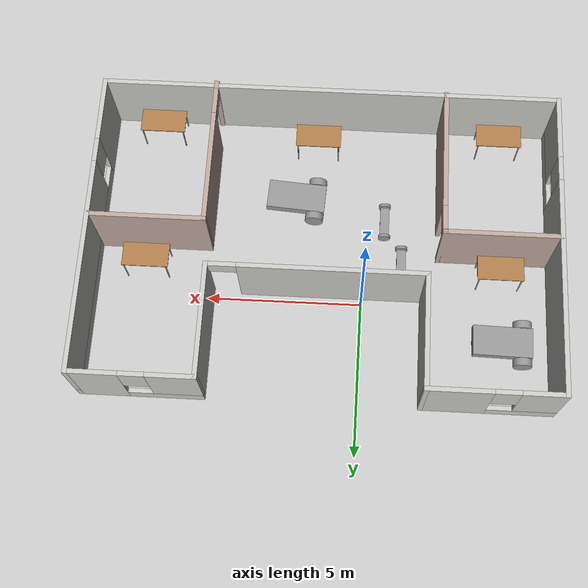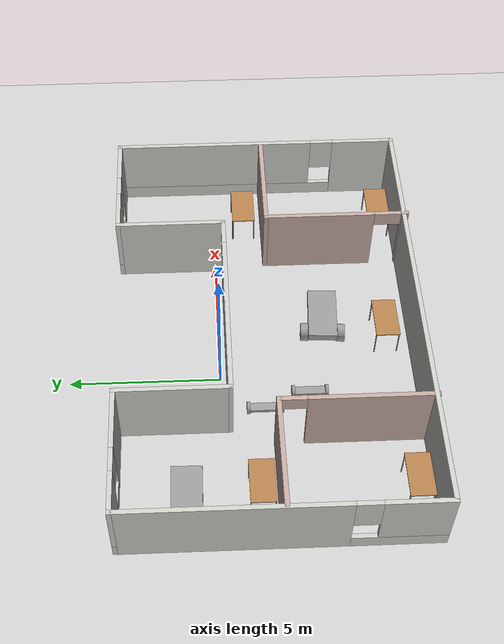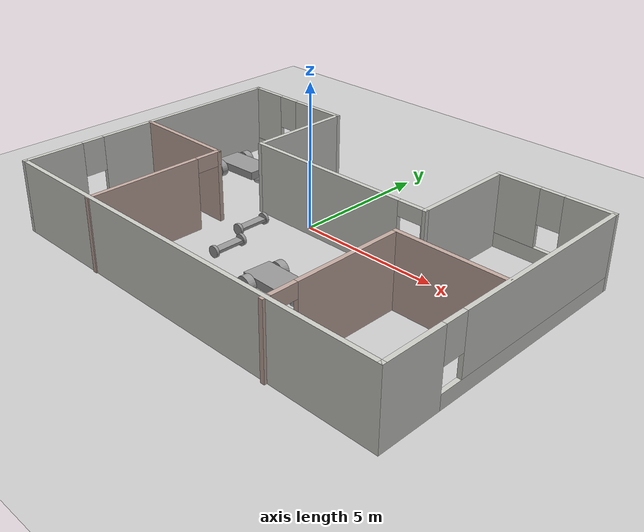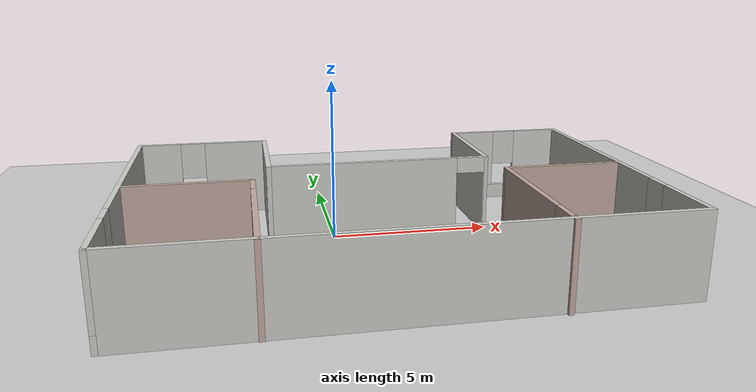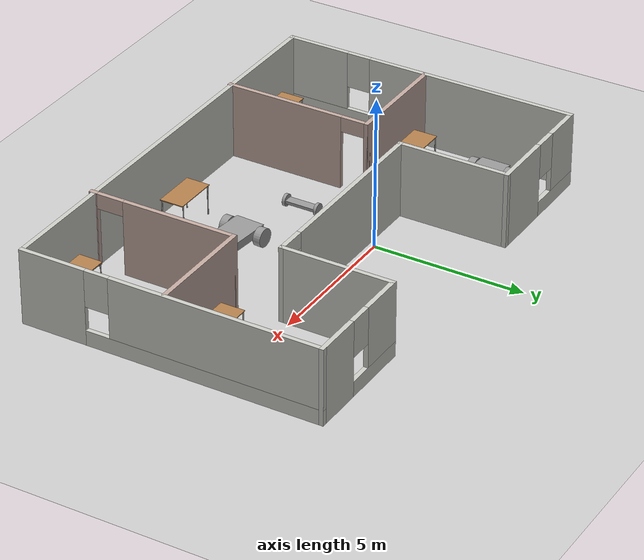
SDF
<sdf version="1.6">
 <world name="default">
  <plugin name="welcome_message" filemane="libwelcome_message.so"/>
  <light name="sun" type="directional">
   <pose>0 0 10 0 -0 0</pose>
   <diffuse>0.8 0.8 0.8 1</diffuse>
   <specular>0.2 0.2 0.2 1</specular>
   <attenuation>
    <range>1000</range>
    <constant>0.9</constant>
    <linear>0.01</linear>
    <quadratic>0.001</quadratic>
   </attenuation>
   <direction>-0.5 0.1 -0.9</direction>
  </light>
  <model name="ground_plane">
   <static>1</static>
   <link name="link">
    <collision name="collision">
     <geometry><plane><normal>0 0 1</normal><size>100 100</size></plane></geometry>
     <surface>
      <contact><collide_bitmask>65535</collide_bitmask></contact>
      <friction><ode><mu>100</mu><mu2>50</mu2></ode></friction>
     </surface>
    </collision>
    <visual name="visual">
     <cast_shadows>0</cast_shadows>
     <geometry><plane><normal>0 0 1</normal><size>100 100</size></plane></geometry>
     <material>
      <script><uri>file://media/materials/scripts/gazebo.material</uri><name>Gazebo/Grey</name></script>
     </material>
    </visual>
   </link>
  </model>
  <gravity>0 0 -9.8</gravity>
  <magnetic_field>6e-06 2.3e-05 -4.2e-05</magnetic_field>
  <atmosphere type="adiabatic"/>
  <physics name="default_physics" default="0" type="ode">
   <max_step_size>0.001</max_step_size>
   <real_time_factor>1</real_time_factor>
   <real_time_update_rate>1000</real_time_update_rate>
  </physics>
  <scene><ambient>0.4 0.4 0.4 1</ambient><background>0.7 0.7 0.7 1</background><shadows>1</shadows></scene>
  <spherical_coordinates>
   <surface_model>EARTH_WGS84</surface_model>
   <latitude_deg>0</latitude_deg>
   <longitude_deg>0</longitude_deg>
   <elevation>0</elevation>
   <heading_deg>0</heading_deg>
  </spherical_coordinates>
  <model name="model">
   <pose>1.27977 -1.64783 0 0 -0 0</pose>
   <link name="Wall_1">
    <pose>-7.425 0.045582 0 0 0 -1.5708</pose>
    <visual name="Wall_1_Visual_0">
     <pose>-1.46661 0 1.25 0 -0 0</pose>
     <geometry><box><size>7.06677 0.15 2.5</size></box></geometry>
     <material>
      <script><uri>file://media/materials/scripts/gazebo.material</uri><name>Gazebo/CeilingTiled</name></script>
      <ambient>1 1 1 1</ambient>
     </material>
     <meta><layer>0</layer></meta>
    </visual>
    <collision name="Wall_1_Collision_0">
     <geometry><box><size>7.06677 0.15 2.5</size></box></geometry>
     <pose>-1.46661 0 1.25 0 -0 0</pose>
    </collision>
    <visual name="Wall_1_Visual_1">
     <pose>3.53339 0 0.25 0 -0 0</pose>
     <geometry><box><size>2.93323 0.15 0.5</size></box></geometry>
     <material>
      <script><uri>file://media/materials/scripts/gazebo.material</uri><name>Gazebo/CeilingTiled</name></script>
      <ambient>1 1 1 1</ambient>
     </material>
     <meta><layer>0</layer></meta>
    </visual>
    <collision name="Wall_1_Collision_1">
     <geometry><box><size>2.93323 0.15 0.5</size></box></geometry>
     <pose>3.53339 0 0.25 0 -0 0</pose>
    </collision>
    <visual name="Wall_1_Visual_2">
     <pose>3.93339 0 1.5 0 -0 0</pose>
     <geometry><box><size>2.13323 0.15 2</size></box></geometry>
     <material>
      <script><uri>file://media/materials/scripts/gazebo.material</uri><name>Gazebo/CeilingTiled</name></script>
      <ambient>1 1 1 1</ambient>
     </material>
     <meta><layer>0</layer></meta>
    </visual>
    <collision name="Wall_1_Collision_2">
     <geometry><box><size>2.13323 0.15 2</size></box></geometry>
     <pose>3.93339 0 1.5 0 -0 0</pose>
    </collision>
    <visual name="Wall_1_Visual_3">
     <pose>2.46677 0 1.9 0 -0 0</pose>
     <geometry><box><size>0.8 0.15 1.2</size></box></geometry>
     <material>
      <script><uri>file://media/materials/scripts/gazebo.material</uri><name>Gazebo/CeilingTiled</name></script>
      <ambient>1 1 1 1</ambient>
     </material>
     <meta><layer>0</layer></meta>
    </visual>
    <collision name="Wall_1_Collision_3">
     <geometry><box><size>0.8 0.15 1.2</size></box></geometry>
     <pose>2.46677 0 1.9 0 -0 0</pose>
    </collision>
   </link>
   <link name="Wall_10">
    <collision name="Wall_10_Collision">
     <geometry><box><size>3.75 0.15 2.5</size></box></geometry>
     <pose>0 0 1.25 0 -0 0</pose>
    </collision>
    <visual name="Wall_10_Visual">
     <pose>0 0 1.25 0 -0 0</pose>
     <geometry><box><size>3.75 0.15 2.5</size></box></geometry>
     <material>
      <script><uri>file://media/materials/scripts/gazebo.material</uri><name>Gazebo/Grey</name></script>
      <ambient>0.760784 0.662745 0.627451 1</ambient>
     </material>
     <meta><layer>0</layer></meta>
    </visual>
    <pose>-5.57831 -0.067079 0 0 -0 0</pose>
   </link>
   <link name="Wall_11">
    <pose>-3.77832 -2.49208 0 0 0 -1.5708</pose>
    <visual name="Wall_11_Visual_0">
     <pose>-2.47349 0 1.25 0 -0 0</pose>
     <geometry><box><size>0.05302 0.15 2.5</size></box></geometry>
     <material>
      <script><uri>file://media/materials/scripts/gazebo.material</uri><name>Gazebo/Grey</name></script>
      <ambient>0.760784 0.662745 0.627451 1</ambient>
     </material>
     <meta><layer>0</layer></meta>
    </visual>
    <collision name="Wall_11_Collision_0">
     <geometry><box><size>0.05302 0.15 2.5</size></box></geometry>
     <pose>-2.47349 0 1.25 0 -0 0</pose>
    </collision>
    <visual name="Wall_11_Visual_1">
     <pose>0.47651 0 1.25 0 -0 0</pose>
     <geometry><box><size>4.04698 0.15 2.5</size></box></geometry>
     <material>
      <script><uri>file://media/materials/scripts/gazebo.material</uri><name>Gazebo/Grey</name></script>
      <ambient>0.760784 0.662745 0.627451 1</ambient>
     </material>
     <meta><layer>0</layer></meta>
    </visual>
    <collision name="Wall_11_Collision_1">
     <geometry><box><size>4.04698 0.15 2.5</size></box></geometry>
     <pose>0.47651 0 1.25 0 -0 0</pose>
    </collision>
    <visual name="Wall_11_Visual_2">
     <pose>-1.99698 0 2.25 0 -0 0</pose>
     <geometry><box><size>0.9 0.15 0.5</size></box></geometry>
     <material>
      <script><uri>file://media/materials/scripts/gazebo.material</uri><name>Gazebo/Grey</name></script>
      <ambient>0.760784 0.662745 0.627451 1</ambient>
     </material>
     <meta><layer>0</layer></meta>
    </visual>
    <collision name="Wall_11_Collision_2">
     <geometry><box><size>0.9 0.15 0.5</size></box></geometry>
     <pose>-1.99698 0 2.25 0 -0 0</pose>
    </collision>
   </link>
   <link name="Wall_13">
    <collision name="Wall_13_Collision">
     <geometry><box><size>3.75 0.15 2.5</size></box></geometry>
     <pose>0 0 1.25 0 -0 0</pose>
    </collision>
    <visual name="Wall_13_Visual">
     <pose>0 0 1.25 0 -0 0</pose>
     <geometry><box><size>3.75 0.15 2.5</size></box></geometry>
     <material>
      <script><uri>file://media/materials/scripts/gazebo.material</uri><name>Gazebo/Grey</name></script>
      <ambient>0.760784 0.662745 0.627451 1</ambient>
     </material>
     <meta><layer>0</layer></meta>
    </visual>
    <pose>5.56162 -0.120582 0 0 -0 3.14159</pose>
   </link>
   <link name="Wall_14">
    <pose>3.76162 -2.54558 0 0 0 -1.5708</pose>
    <visual name="Wall_14_Visual_0">
     <pose>-0.587527 0 1.25 0 -0 0</pose>
     <geometry><box><size>3.82495 0.15 2.5</size></box></geometry>
     <material>
      <script><uri>file://media/materials/scripts/gazebo.material</uri><name>Gazebo/Grey</name></script>
      <ambient>0.760784 0.662745 0.627451 1</ambient>
     </material>
     <meta><layer>0</layer></meta>
    </visual>
    <collision name="Wall_14_Collision_0">
     <geometry><box><size>3.82495 0.15 2.5</size></box></geometry>
     <pose>-0.587527 0 1.25 0 -0 0</pose>
    </collision>
    <visual name="Wall_14_Visual_1">
     <pose>2.36247 0 1.25 0 -0 0</pose>
     <geometry><box><size>0.275054 0.15 2.5</size></box></geometry>
     <material>
      <script><uri>file://media/materials/scripts/gazebo.material</uri><name>Gazebo/Grey</name></script>
      <ambient>0.760784 0.662745 0.627451 1</ambient>
     </material>
     <meta><layer>0</layer></meta>
    </visual>
    <collision name="Wall_14_Collision_1">
     <geometry><box><size>0.275054 0.15 2.5</size></box></geometry>
     <pose>2.36247 0 1.25 0 -0 0</pose>
    </collision>
    <visual name="Wall_14_Visual_2">
     <pose>1.77495 0 2.25 0 -0 0</pose>
     <geometry><box><size>0.9 0.15 0.5</size></box></geometry>
     <material>
      <script><uri>file://media/materials/scripts/gazebo.material</uri><name>Gazebo/Grey</name></script>
      <ambient>0.760784 0.662745 0.627451 1</ambient>
     </material>
     <meta><layer>0</layer></meta>
    </visual>
    <collision name="Wall_14_Collision_2">
     <geometry><box><size>0.9 0.15 0.5</size></box></geometry>
     <pose>1.77495 0 2.25 0 -0 0</pose>
    </collision>
   </link>
   <link name="Wall_2">
    <collision name="Wall_2_Collision">
     <geometry><box><size>15 0.15 2.5</size></box></geometry>
     <pose>0 0 1.25 0 -0 0</pose>
    </collision>
    <visual name="Wall_2_Visual">
     <pose>0 0 1.25 0 -0 0</pose>
     <geometry><box><size>15 0.15 2.5</size></box></geometry>
     <material>
      <script><uri>file://media/materials/scripts/gazebo.material</uri><name>Gazebo/CeilingTiled</name></script>
      <ambient>1 1 1 1</ambient>
     </material>
     <meta><layer>0</layer></meta>
    </visual>
    <pose>0 -4.87942 0 0 -0 0</pose>
   </link>
   <link name="Wall_3">
    <pose>7.425 0.045582 0 0 -0 1.5708</pose>
    <visual name="Wall_3_Visual_0">
     <pose>-3.89326 0 1.25 0 -0 0</pose>
     <geometry><box><size>2.21348 0.15 2.5</size></box></geometry>
     <material>
      <script><uri>file://media/materials/scripts/gazebo.material</uri><name>Gazebo/CeilingTiled</name></script>
      <ambient>1 1 1 1</ambient>
     </material>
     <meta><layer>0</layer></meta>
    </visual>
    <collision name="Wall_3_Collision_0">
     <geometry><box><size>2.21348 0.15 2.5</size></box></geometry>
     <pose>-3.89326 0 1.25 0 -0 0</pose>
    </collision>
    <visual name="Wall_3_Visual_1">
     <pose>1.10674 0 0.25 0 -0 0</pose>
     <geometry><box><size>7.78652 0.15 0.5</size></box></geometry>
     <material>
      <script><uri>file://media/materials/scripts/gazebo.material</uri><name>Gazebo/CeilingTiled</name></script>
      <ambient>1 1 1 1</ambient>
     </material>
     <meta><layer>0</layer></meta>
    </visual>
    <collision name="Wall_3_Collision_1">
     <geometry><box><size>7.78652 0.15 0.5</size></box></geometry>
     <pose>1.10674 0 0.25 0 -0 0</pose>
    </collision>
    <visual name="Wall_3_Visual_2">
     <pose>1.50674 0 1.5 0 -0 0</pose>
     <geometry><box><size>6.98652 0.15 2</size></box></geometry>
     <material>
      <script><uri>file://media/materials/scripts/gazebo.material</uri><name>Gazebo/CeilingTiled</name></script>
      <ambient>1 1 1 1</ambient>
     </material>
     <meta><layer>0</layer></meta>
    </visual>
    <collision name="Wall_3_Collision_2">
     <geometry><box><size>6.98652 0.15 2</size></box></geometry>
     <pose>1.50674 0 1.5 0 -0 0</pose>
    </collision>
    <visual name="Wall_3_Visual_3">
     <pose>-2.38652 0 1.9 0 -0 0</pose>
     <geometry><box><size>0.8 0.15 1.2</size></box></geometry>
     <material>
      <script><uri>file://media/materials/scripts/gazebo.material</uri><name>Gazebo/CeilingTiled</name></script>
      <ambient>1 1 1 1</ambient>
     </material>
     <meta><layer>0</layer></meta>
    </visual>
    <collision name="Wall_3_Collision_3">
     <geometry><box><size>0.8 0.15 1.2</size></box></geometry>
     <pose>-2.38652 0 1.9 0 -0 0</pose>
    </collision>
   </link>
   <link name="Wall_4">
    <pose>5.5 4.97058 0 0 -0 3.14159</pose>
    <visual name="Wall_4_Visual_0">
     <pose>-1.18114 0 1.25 0 -0 0</pose>
     <geometry><box><size>1.63771 0.15 2.5</size></box></geometry>
     <material>
      <script><uri>file://media/materials/scripts/gazebo.material</uri><name>Gazebo/CeilingTiled</name></script>
      <ambient>1 1 1 1</ambient>
     </material>
     <meta><layer>0</layer></meta>
    </visual>
    <collision name="Wall_4_Collision_0">
     <geometry><box><size>1.63771 0.15 2.5</size></box></geometry>
     <pose>-1.18114 0 1.25 0 -0 0</pose>
    </collision>
    <visual name="Wall_4_Visual_1">
     <pose>0.818857 0 0.25 0 -0 0</pose>
     <geometry><box><size>2.36229 0.15 0.5</size></box></geometry>
     <material>
      <script><uri>file://media/materials/scripts/gazebo.material</uri><name>Gazebo/CeilingTiled</name></script>
      <ambient>1 1 1 1</ambient>
     </material>
     <meta><layer>0</layer></meta>
    </visual>
    <collision name="Wall_4_Collision_1">
     <geometry><box><size>2.36229 0.15 0.5</size></box></geometry>
     <pose>0.818857 0 0.25 0 -0 0</pose>
    </collision>
    <visual name="Wall_4_Visual_2">
     <pose>1.21886 0 1.5 0 -0 0</pose>
     <geometry><box><size>1.56229 0.15 2</size></box></geometry>
     <material>
      <script><uri>file://media/materials/scripts/gazebo.material</uri><name>Gazebo/CeilingTiled</name></script>
      <ambient>1 1 1 1</ambient>
     </material>
     <meta><layer>0</layer></meta>
    </visual>
    <collision name="Wall_4_Collision_2">
     <geometry><box><size>1.56229 0.15 2</size></box></geometry>
     <pose>1.21886 0 1.5 0 -0 0</pose>
    </collision>
    <visual name="Wall_4_Visual_3">
     <pose>0.037714 0 1.9 0 -0 0</pose>
     <geometry><box><size>0.8 0.15 1.2</size></box></geometry>
     <material>
      <script><uri>file://media/materials/scripts/gazebo.material</uri><name>Gazebo/CeilingTiled</name></script>
      <ambient>1 1 1 1</ambient>
     </material>
     <meta><layer>0</layer></meta>
    </visual>
    <collision name="Wall_4_Collision_3">
     <geometry><box><size>0.8 0.15 1.2</size></box></geometry>
     <pose>0.037714 0 1.9 0 -0 0</pose>
    </collision>
   </link>
   <link name="Wall_5">
    <collision name="Wall_5_Collision">
     <geometry><box><size>3.75 0.15 2.5</size></box></geometry>
     <pose>0 0 1.25 0 -0 0</pose>
    </collision>
    <visual name="Wall_5_Visual">
     <pose>0 0 1.25 0 -0 0</pose>
     <geometry><box><size>3.75 0.15 2.5</size></box></geometry>
     <material>
      <script><uri>file://media/materials/scripts/gazebo.material</uri><name>Gazebo/CeilingTiled</name></script>
      <ambient>1 1 1 1</ambient>
     </material>
     <meta><layer>0</layer></meta>
    </visual>
    <pose>3.575 3.17058 0 0 0 -1.5708</pose>
   </link>
   <link name="Wall_6">
    <pose>0.15 1.37058 0 0 -0 3.14159</pose>
    <visual name="Wall_6_Visual_0">
     <pose>-3.44071 0 1.25 0 -0 0</pose>
     <geometry><box><size>0.118576 0.15 2.5</size></box></geometry>
     <material>
      <script><uri>file://media/materials/scripts/gazebo.material</uri><name>Gazebo/CeilingTiled</name></script>
      <ambient>1 1 1 1</ambient>
     </material>
     <meta><layer>0</layer></meta>
    </visual>
    <collision name="Wall_6_Collision_0">
     <geometry><box><size>0.118576 0.15 2.5</size></box></geometry>
     <pose>-3.44071 0 1.25 0 -0 0</pose>
    </collision>
    <visual name="Wall_6_Visual_1">
     <pose>0.509288 0 1.25 0 -0 0</pose>
     <geometry><box><size>5.98142 0.15 2.5</size></box></geometry>
     <material>
      <script><uri>file://media/materials/scripts/gazebo.material</uri><name>Gazebo/CeilingTiled</name></script>
      <ambient>1 1 1 1</ambient>
     </material>
     <meta><layer>0</layer></meta>
    </visual>
    <collision name="Wall_6_Collision_1">
     <geometry><box><size>5.98142 0.15 2.5</size></box></geometry>
     <pose>0.509288 0 1.25 0 -0 0</pose>
    </collision>
    <visual name="Wall_6_Visual_2">
     <pose>-2.93142 0 2.25 0 -0 0</pose>
     <geometry><box><size>0.9 0.15 0.5</size></box></geometry>
     <material>
      <script><uri>file://media/materials/scripts/gazebo.material</uri><name>Gazebo/CeilingTiled</name></script>
      <ambient>1 1 1 1</ambient>
     </material>
     <meta><layer>0</layer></meta>
    </visual>
    <collision name="Wall_6_Collision_2">
     <geometry><box><size>0.9 0.15 0.5</size></box></geometry>
     <pose>-2.93142 0 2.25 0 -0 0</pose>
    </collision>
   </link>
   <link name="Wall_7">
    <collision name="Wall_7_Collision">
     <geometry><box><size>3.75 0.15 2.5</size></box></geometry>
     <pose>0 0 1.25 0 -0 0</pose>
    </collision>
    <visual name="Wall_7_Visual">
     <pose>0 0 1.25 0 -0 0</pose>
     <geometry><box><size>3.75 0.15 2.5</size></box></geometry>
     <material>
      <script><uri>file://media/materials/scripts/gazebo.material</uri><name>Gazebo/CeilingTiled</name></script>
      <ambient>1 1 1 1</ambient>
     </material>
     <meta><layer>0</layer></meta>
    </visual>
    <pose>-3.275 3.17058 0 0 -0 1.5708</pose>
   </link>
   <link name="Wall_8">
    <pose>-5.35 4.97058 0 0 -0 3.14159</pose>
    <visual name="Wall_8_Visual_0">
     <pose>-1.10351 0 1.25 0 -0 0</pose>
     <geometry><box><size>2.09299 0.15 2.5</size></box></geometry>
     <material>
      <script><uri>file://media/materials/scripts/gazebo.material</uri><name>Gazebo/CeilingTiled</name></script>
      <ambient>1 1 1 1</ambient>
     </material>
     <meta><layer>0</layer></meta>
    </visual>
    <collision name="Wall_8_Collision_0">
     <geometry><box><size>2.09299 0.15 2.5</size></box></geometry>
     <pose>-1.10351 0 1.25 0 -0 0</pose>
    </collision>
    <visual name="Wall_8_Visual_1">
     <pose>1.04649 0 0.25 0 -0 0</pose>
     <geometry><box><size>2.20701 0.15 0.5</size></box></geometry>
     <material>
      <script><uri>file://media/materials/scripts/gazebo.material</uri><name>Gazebo/CeilingTiled</name></script>
      <ambient>1 1 1 1</ambient>
     </material>
     <meta><layer>0</layer></meta>
    </visual>
    <collision name="Wall_8_Collision_1">
     <geometry><box><size>2.20701 0.15 0.5</size></box></geometry>
     <pose>1.04649 0 0.25 0 -0 0</pose>
    </collision>
    <visual name="Wall_8_Visual_2">
     <pose>1.44649 0 1.5 0 -0 0</pose>
     <geometry><box><size>1.40701 0.15 2</size></box></geometry>
     <material>
      <script><uri>file://media/materials/scripts/gazebo.material</uri><name>Gazebo/CeilingTiled</name></script>
      <ambient>1 1 1 1</ambient>
     </material>
     <meta><layer>0</layer></meta>
    </visual>
    <collision name="Wall_8_Collision_2">
     <geometry><box><size>1.40701 0.15 2</size></box></geometry>
     <pose>1.44649 0 1.5 0 -0 0</pose>
    </collision>
    <visual name="Wall_8_Visual_3">
     <pose>0.342986 0 1.9 0 -0 0</pose>
     <geometry><box><size>0.8 0.15 1.2</size></box></geometry>
     <material>
      <script><uri>file://media/materials/scripts/gazebo.material</uri><name>Gazebo/CeilingTiled</name></script>
      <ambient>1 1 1 1</ambient>
     </material>
     <meta><layer>0</layer></meta>
    </visual>
    <collision name="Wall_8_Collision_3">
     <geometry><box><size>0.8 0.15 1.2</size></box></geometry>
     <pose>0.342986 0 1.9 0 -0 0</pose>
    </collision>
   </link>
   <static>1</static>
  </model>
  <model name="model_0">
   <link name="link_0_clone">
    <pose>0.127631 -1.05362 0.2 0 -0 0</pose>
    <inertial>
     <mass>1</mass>
     <inertia>
      <ixx>0.166667</ixx>
      <ixy>0</ixy>
      <ixz>0</ixz>
      <iyy>0.166667</iyy>
      <iyz>0</iyz>
      <izz>0.166667</izz>
     </inertia>
    </inertial>
    <visual name="visual">
     <geometry><box><size>0.3 1 0.1</size></box></geometry>
     <material>
      <lighting>1</lighting>
      <script><uri>file://media/materials/scripts/gazebo.material</uri><name>Gazebo/Grey</name></script>
      <shader type="pixel"><normal_map>__default__</normal_map></shader>
      <ambient>0.3 0.3 0.3 1</ambient>
      <diffuse>0.7 0.7 0.7 1</diffuse>
      <specular>0.01 0.01 0.01 1</specular>
      <emissive>0 0 0 1</emissive>
     </material>
    </visual>
    <collision name="collision">
     <geometry><box><size>0.3 1 0.1</size></box></geometry>
     <surface>
      <friction>
       <ode><mu>1</mu><mu2>1</mu2><fdir1>0 0 0</fdir1><slip1>0</slip1><slip2>0</slip2></ode>
       <torsional>
        <coefficient>1</coefficient>
        <patch_radius>0</patch_radius>
        <surface_radius>0</surface_radius>
        <use_patch_radius>1</use_patch_radius>
        <ode><slip>0</slip></ode>
       </torsional>
      </friction>
      <bounce><restitution_coefficient>0</restitution_coefficient><threshold>1e+06</threshold></bounce>
      <contact>
       <collide_without_contact>0</collide_without_contact>
       <collide_without_contact_bitmask>1</collide_without_contact_bitmask>
       <collide_bitmask>1</collide_bitmask>
       <ode>
        <soft_cfm>0</soft_cfm>
        <soft_erp>0.2</soft_erp>
        <kp>1e+13</kp>
        <kd>1</kd>
        <max_vel>0.01</max_vel>
        <min_depth>0</min_depth>
       </ode>
       <bullet>
        <split_impulse>1</split_impulse>
        <split_impulse_penetration_threshold>-0.01</split_impulse_penetration_threshold>
        <soft_cfm>0</soft_cfm>
        <soft_erp>0.2</soft_erp>
        <kp>1e+13</kp>
        <kd>1</kd>
       </bullet>
      </contact>
     </surface>
    </collision>
   </link>
   <link name="link_0_clone_clone">
    <pose>0.715383 -2.55052 0.2 0 -0 0</pose>
    <inertial>
     <mass>1</mass>
     <inertia>
      <ixx>0.166667</ixx>
      <ixy>0</ixy>
      <ixz>0</ixz>
      <iyy>0.166667</iyy>
      <iyz>0</iyz>
      <izz>0.166667</izz>
     </inertia>
    </inertial>
    <visual name="visual">
     <geometry><box><size>0.3 1 0.1</size></box></geometry>
     <material>
      <lighting>1</lighting>
      <script><uri>file://media/materials/scripts/gazebo.material</uri><name>Gazebo/Grey</name></script>
      <shader type="pixel"><normal_map>__default__</normal_map></shader>
      <ambient>0.3 0.3 0.3 1</ambient>
      <diffuse>0.7 0.7 0.7 1</diffuse>
      <specular>0.01 0.01 0.01 1</specular>
      <emissive>0 0 0 1</emissive>
     </material>
    </visual>
    <collision name="collision">
     <geometry><box><size>0.3 1 0.1</size></box></geometry>
     <surface>
      <friction>
       <ode><mu>1</mu><mu2>1</mu2><fdir1>0 0 0</fdir1><slip1>0</slip1><slip2>0</slip2></ode>
       <torsional>
        <coefficient>1</coefficient>
        <patch_radius>0</patch_radius>
        <surface_radius>0</surface_radius>
        <use_patch_radius>1</use_patch_radius>
        <ode><slip>0</slip></ode>
       </torsional>
      </friction>
      <bounce><restitution_coefficient>0</restitution_coefficient><threshold>1e+06</threshold></bounce>
      <contact>
       <collide_without_contact>0</collide_without_contact>
       <collide_without_contact_bitmask>1</collide_without_contact_bitmask>
       <collide_bitmask>1</collide_bitmask>
       <ode>
        <soft_cfm>0</soft_cfm>
        <soft_erp>0.2</soft_erp>
        <kp>1e+13</kp>
        <kd>1</kd>
        <max_vel>0.01</max_vel>
        <min_depth>0</min_depth>
       </ode>
       <bullet>
        <split_impulse>1</split_impulse>
        <split_impulse_penetration_threshold>-0.01</split_impulse_penetration_threshold>
        <soft_cfm>0</soft_cfm>
        <soft_erp>0.2</soft_erp>
        <kp>1e+13</kp>
        <kd>1</kd>
       </bullet>
      </contact>
     </surface>
    </collision>
   </link>
   <link name="link_1_clone">
    <pose>0.127631 -1.60364 0.2 1.5707 -0 0</pose>
    <inertial>
     <mass>1</mass>
     <inertia><ixx>0.145833</ixx><ixy>0</ixy><ixz>0</ixz><iyy>0.145833</iyy><iyz>0</iyz><izz>0.125</izz></inertia>
    </inertial>
    <visual name="visual">
     <geometry><cylinder><radius>0.2</radius><length>0.1</length></cylinder></geometry>
     <material>
      <lighting>1</lighting>
      <script><uri>file://media/materials/scripts/gazebo.material</uri><name>Gazebo/Grey</name></script>
      <shader type="pixel"><normal_map>__default__</normal_map></shader>
      <ambient>0.3 0.3 0.3 1</ambient>
      <diffuse>0.7 0.7 0.7 1</diffuse>
      <specular>0.01 0.01 0.01 1</specular>
      <emissive>0 0 0 1</emissive>
     </material>
    </visual>
    <collision name="collision">
     <geometry><cylinder><radius>0.2</radius><length>0.1</length></cylinder></geometry>
     <surface>
      <friction>
       <ode><mu>1</mu><mu2>1</mu2><fdir1>0 0 0</fdir1><slip1>0</slip1><slip2>0</slip2></ode>
       <torsional>
        <coefficient>1</coefficient>
        <patch_radius>0</patch_radius>
        <surface_radius>0</surface_radius>
        <use_patch_radius>1</use_patch_radius>
        <ode><slip>0</slip></ode>
       </torsional>
      </friction>
      <bounce><restitution_coefficient>0</restitution_coefficient><threshold>1e+06</threshold></bounce>
      <contact>
       <collide_without_contact>0</collide_without_contact>
       <collide_without_contact_bitmask>1</collide_without_contact_bitmask>
       <collide_bitmask>1</collide_bitmask>
       <ode>
        <soft_cfm>0</soft_cfm>
        <soft_erp>0.2</soft_erp>
        <kp>1e+13</kp>
        <kd>1</kd>
        <max_vel>0.01</max_vel>
        <min_depth>0</min_depth>
       </ode>
       <bullet>
        <split_impulse>1</split_impulse>
        <split_impulse_penetration_threshold>-0.01</split_impulse_penetration_threshold>
        <soft_cfm>0</soft_cfm>
        <soft_erp>0.2</soft_erp>
        <kp>1e+13</kp>
        <kd>1</kd>
       </bullet>
      </contact>
     </surface>
    </collision>
   </link>
   <link name="link_1_clone_clone">
    <pose>0.127631 -0.5036 0.2 1.5707 -0 0</pose>
    <inertial>
     <mass>1</mass>
     <inertia><ixx>0.145833</ixx><ixy>0</ixy><ixz>0</ixz><iyy>0.145833</iyy><iyz>0</iyz><izz>0.125</izz></inertia>
    </inertial>
    <visual name="visual">
     <geometry><cylinder><radius>0.2</radius><length>0.1</length></cylinder></geometry>
     <material>
      <lighting>1</lighting>
      <script><uri>file://media/materials/scripts/gazebo.material</uri><name>Gazebo/Grey</name></script>
      <shader type="pixel"><normal_map>__default__</normal_map></shader>
      <ambient>0.3 0.3 0.3 1</ambient>
      <diffuse>0.7 0.7 0.7 1</diffuse>
      <specular>0.01 0.01 0.01 1</specular>
      <emissive>0 0 0 1</emissive>
     </material>
    </visual>
    <collision name="collision">
     <geometry><cylinder><radius>0.2</radius><length>0.1</length></cylinder></geometry>
     <surface>
      <friction>
       <ode><mu>1</mu><mu2>1</mu2><fdir1>0 0 0</fdir1><slip1>0</slip1><slip2>0</slip2></ode>
       <torsional>
        <coefficient>1</coefficient>
        <patch_radius>0</patch_radius>
        <surface_radius>0</surface_radius>
        <use_patch_radius>1</use_patch_radius>
        <ode><slip>0</slip></ode>
       </torsional>
      </friction>
      <bounce><restitution_coefficient>0</restitution_coefficient><threshold>1e+06</threshold></bounce>
      <contact>
       <collide_without_contact>0</collide_without_contact>
       <collide_without_contact_bitmask>1</collide_without_contact_bitmask>
       <collide_bitmask>1</collide_bitmask>
       <ode>
        <soft_cfm>0</soft_cfm>
        <soft_erp>0.2</soft_erp>
        <kp>1e+13</kp>
        <kd>1</kd>
        <max_vel>0.01</max_vel>
        <min_depth>0</min_depth>
       </ode>
       <bullet>
        <split_impulse>1</split_impulse>
        <split_impulse_penetration_threshold>-0.01</split_impulse_penetration_threshold>
        <soft_cfm>0</soft_cfm>
        <soft_erp>0.2</soft_erp>
        <kp>1e+13</kp>
        <kd>1</kd>
       </bullet>
      </contact>
     </surface>
    </collision>
   </link>
   <link name="link_1_clone_clone_0">
    <pose>0.715383 -2.0005 0.2 1.5707 -0 0</pose>
    <inertial>
     <mass>1</mass>
     <inertia><ixx>0.145833</ixx><ixy>0</ixy><ixz>0</ixz><iyy>0.145833</iyy><iyz>0</iyz><izz>0.125</izz></inertia>
    </inertial>
    <visual name="visual">
     <geometry><cylinder><radius>0.2</radius><length>0.1</length></cylinder></geometry>
     <material>
      <lighting>1</lighting>
      <script><uri>file://media/materials/scripts/gazebo.material</uri><name>Gazebo/Grey</name></script>
      <shader type="pixel"><normal_map>__default__</normal_map></shader>
      <ambient>0.3 0.3 0.3 1</ambient>
      <diffuse>0.7 0.7 0.7 1</diffuse>
      <specular>0.01 0.01 0.01 1</specular>
      <emissive>0 0 0 1</emissive>
     </material>
    </visual>
    <collision name="collision">
     <geometry><cylinder><radius>0.2</radius><length>0.1</length></cylinder></geometry>
     <surface>
      <friction>
       <ode><mu>1</mu><mu2>1</mu2><fdir1>0 0 0</fdir1><slip1>0</slip1><slip2>0</slip2></ode>
       <torsional>
        <coefficient>1</coefficient>
        <patch_radius>0</patch_radius>
        <surface_radius>0</surface_radius>
        <use_patch_radius>1</use_patch_radius>
        <ode><slip>0</slip></ode>
       </torsional>
      </friction>
      <bounce><restitution_coefficient>0</restitution_coefficient><threshold>1e+06</threshold></bounce>
      <contact>
       <collide_without_contact>0</collide_without_contact>
       <collide_without_contact_bitmask>1</collide_without_contact_bitmask>
       <collide_bitmask>1</collide_bitmask>
       <ode>
        <soft_cfm>0</soft_cfm>
        <soft_erp>0.2</soft_erp>
        <kp>1e+13</kp>
        <kd>1</kd>
        <max_vel>0.01</max_vel>
        <min_depth>0</min_depth>
       </ode>
       <bullet>
        <split_impulse>1</split_impulse>
        <split_impulse_penetration_threshold>-0.01</split_impulse_penetration_threshold>
        <soft_cfm>0</soft_cfm>
        <soft_erp>0.2</soft_erp>
        <kp>1e+13</kp>
        <kd>1</kd>
       </bullet>
      </contact>
     </surface>
    </collision>
   </link>
   <link name="link_1_clone_clone_clone">
    <pose>0.715383 -3.10054 0.2 1.5707 -0 0</pose>
    <inertial>
     <mass>1</mass>
     <inertia><ixx>0.145833</ixx><ixy>0</ixy><ixz>0</ixz><iyy>0.145833</iyy><iyz>0</iyz><izz>0.125</izz></inertia>
    </inertial>
    <visual name="visual">
     <geometry><cylinder><radius>0.2</radius><length>0.1</length></cylinder></geometry>
     <material>
      <lighting>1</lighting>
      <script><uri>file://media/materials/scripts/gazebo.material</uri><name>Gazebo/Grey</name></script>
      <shader type="pixel"><normal_map>__default__</normal_map></shader>
      <ambient>0.3 0.3 0.3 1</ambient>
      <diffuse>0.7 0.7 0.7 1</diffuse>
      <specular>0.01 0.01 0.01 1</specular>
      <emissive>0 0 0 1</emissive>
     </material>
    </visual>
    <collision name="collision">
     <geometry><cylinder><radius>0.2</radius><length>0.1</length></cylinder></geometry>
     <surface>
      <friction>
       <ode><mu>1</mu><mu2>1</mu2><fdir1>0 0 0</fdir1><slip1>0</slip1><slip2>0</slip2></ode>
       <torsional>
        <coefficient>1</coefficient>
        <patch_radius>0</patch_radius>
        <surface_radius>0</surface_radius>
        <use_patch_radius>1</use_patch_radius>
        <ode><slip>0</slip></ode>
       </torsional>
      </friction>
      <bounce><restitution_coefficient>0</restitution_coefficient><threshold>1e+06</threshold></bounce>
      <contact>
       <collide_without_contact>0</collide_without_contact>
       <collide_without_contact_bitmask>1</collide_without_contact_bitmask>
       <collide_bitmask>1</collide_bitmask>
       <ode>
        <soft_cfm>0</soft_cfm>
        <soft_erp>0.2</soft_erp>
        <kp>1e+13</kp>
        <kd>1</kd>
        <max_vel>0.01</max_vel>
        <min_depth>0</min_depth>
       </ode>
       <bullet>
        <split_impulse>1</split_impulse>
        <split_impulse_penetration_threshold>-0.01</split_impulse_penetration_threshold>
        <soft_cfm>0</soft_cfm>
        <soft_erp>0.2</soft_erp>
        <kp>1e+13</kp>
        <kd>1</kd>
       </bullet>
      </contact>
     </surface>
    </collision>
   </link>
   <joint name="link_0_clone_JOINT_2" type="revolute">
    <parent>link_0_clone</parent>
    <child>link_1_clone</child>
    <axis>
     <xyz>0 0 1</xyz>
     <use_parent_model_frame>0</use_parent_model_frame>
     <limit>
      <lower>-1.79769e+308</lower>
      <upper>1.79769e+308</upper>
      <effort>-1</effort>
      <velocity>-1</velocity>
     </limit>
     <dynamics>
      <spring_reference>0</spring_reference>
      <spring_stiffness>0</spring_stiffness>
      <damping>0</damping>
     </dynamics>
    </axis>
    <physics>
     <ode><limit><cfm>0</cfm><erp>0.2</erp></limit><suspension><cfm>0</cfm><erp>0.2</erp></suspension></ode>
    </physics>
   </joint>
   <joint name="link_0_clone_JOINT_4" type="revolute">
    <parent>link_0_clone</parent>
    <child>link_1_clone_clone</child>
    <axis>
     <xyz>0 0 1</xyz>
     <use_parent_model_frame>0</use_parent_model_frame>
     <limit>
      <lower>-1.79769e+308</lower>
      <upper>1.79769e+308</upper>
      <effort>-1</effort>
      <velocity>-1</velocity>
     </limit>
     <dynamics>
      <spring_reference>0</spring_reference>
      <spring_stiffness>0</spring_stiffness>
      <damping>0</damping>
     </dynamics>
    </axis>
    <physics>
     <ode><limit><cfm>0</cfm><erp>0.2</erp></limit><suspension><cfm>0</cfm><erp>0.2</erp></suspension></ode>
    </physics>
   </joint>
   <joint name="link_0_clone_clone_JOINT_5" type="revolute">
    <parent>link_0_clone_clone</parent>
    <child>link_1_clone_clone_clone</child>
    <axis>
     <xyz>0 0 1</xyz>
     <use_parent_model_frame>0</use_parent_model_frame>
     <limit>
      <lower>-1.79769e+308</lower>
      <upper>1.79769e+308</upper>
      <effort>-1</effort>
      <velocity>-1</velocity>
     </limit>
     <dynamics>
      <spring_reference>0</spring_reference>
      <spring_stiffness>0</spring_stiffness>
      <damping>0</damping>
     </dynamics>
    </axis>
    <physics>
     <ode><limit><cfm>0</cfm><erp>0.2</erp></limit><suspension><cfm>0</cfm><erp>0.2</erp></suspension></ode>
    </physics>
   </joint>
   <joint name="link_0_clone_clone_JOINT_6" type="revolute">
    <parent>link_0_clone_clone</parent>
    <child>link_1_clone_clone_0</child>
    <axis>
     <xyz>0 0 1</xyz>
     <use_parent_model_frame>0</use_parent_model_frame>
     <limit>
      <lower>-1.79769e+308</lower>
      <upper>1.79769e+308</upper>
      <effort>-1</effort>
      <velocity>-1</velocity>
     </limit>
     <dynamics>
      <spring_reference>0</spring_reference>
      <spring_stiffness>0</spring_stiffness>
      <damping>0</damping>
     </dynamics>
    </axis>
    <physics>
     <ode><limit><cfm>0</cfm><erp>0.2</erp></limit><suspension><cfm>0</cfm><erp>0.2</erp></suspension></ode>
    </physics>
   </joint>
   <static>0</static>
   <pose>-1.41122 -0.376056 7e-06 4e-06 -0 0</pose>
  </model>
  <model name="table">
   <static>1</static>
   <link name="link">
    <collision name="surface">
     <pose>0 0 1 0 -0 0</pose>
     <geometry><box><size>1.5 0.8 0.03</size></box></geometry>
     <surface><friction><ode><mu>0.6</mu><mu2>0.6</mu2></ode></friction></surface>
    </collision>
    <visual name="visual1">
     <pose>0 0 1 0 -0 0</pose>
     <geometry><box><size>1.5 0.8 0.03</size></box></geometry>
     <material>
      <script><uri>file://media/materials/scripts/gazebo.material</uri><name>Gazebo/Wood</name></script>
     </material>
    </visual>
    <collision name="front_left_leg">
     <pose>0.68 0.38 0.5 0 -0 0</pose>
     <geometry><cylinder><radius>0.02</radius><length>1</length></cylinder></geometry>
    </collision>
    <visual name="front_left_leg">
     <pose>0.68 0.38 0.5 0 -0 0</pose>
     <geometry><cylinder><radius>0.02</radius><length>1</length></cylinder></geometry>
     <material>
      <script><uri>file://media/materials/scripts/gazebo.material</uri><name>Gazebo/Grey</name></script>
     </material>
    </visual>
    <collision name="front_right_leg">
     <pose>0.68 -0.38 0.5 0 -0 0</pose>
     <geometry><cylinder><radius>0.02</radius><length>1</length></cylinder></geometry>
    </collision>
    <visual name="front_right_leg">
     <pose>0.68 -0.38 0.5 0 -0 0</pose>
     <geometry><cylinder><radius>0.02</radius><length>1</length></cylinder></geometry>
     <material>
      <script><uri>file://media/materials/scripts/gazebo.material</uri><name>Gazebo/Grey</name></script>
     </material>
    </visual>
    <collision name="back_right_leg">
     <pose>-0.68 -0.38 0.5 0 -0 0</pose>
     <geometry><cylinder><radius>0.02</radius><length>1</length></cylinder></geometry>
    </collision>
    <visual name="back_right_leg">
     <pose>-0.68 -0.38 0.5 0 -0 0</pose>
     <geometry><cylinder><radius>0.02</radius><length>1</length></cylinder></geometry>
     <material>
      <script><uri>file://media/materials/scripts/gazebo.material</uri><name>Gazebo/Grey</name></script>
     </material>
    </visual>
    <collision name="back_left_leg">
     <pose>-0.68 0.38 0.5 0 -0 0</pose>
     <geometry><cylinder><radius>0.02</radius><length>1</length></cylinder></geometry>
    </collision>
    <visual name="back_left_leg">
     <pose>-0.68 0.38 0.5 0 -0 0</pose>
     <geometry><cylinder><radius>0.02</radius><length>1</length></cylinder></geometry>
     <material>
      <script><uri>file://media/materials/scripts/gazebo.material</uri><name>Gazebo/Grey</name></script>
     </material>
    </visual>
   </link>
   <pose>1.64308 -5.63445 0 0 -0 0</pose>
  </model>
  <model name="table_0">
   <static>1</static>
   <link name="link">
    <collision name="surface">
     <pose>0 0 1 0 -0 0</pose>
     <geometry><box><size>1.5 0.8 0.03</size></box></geometry>
     <surface><friction><ode><mu>0.6</mu><mu2>0.6</mu2></ode></friction></surface>
    </collision>
    <visual name="visual1">
     <pose>0 0 1 0 -0 0</pose>
     <geometry><box><size>1.5 0.8 0.03</size></box></geometry>
     <material>
      <script><uri>file://media/materials/scripts/gazebo.material</uri><name>Gazebo/Wood</name></script>
     </material>
    </visual>
    <collision name="front_left_leg">
     <pose>0.68 0.38 0.5 0 -0 0</pose>
     <geometry><cylinder><radius>0.02</radius><length>1</length></cylinder></geometry>
    </collision>
    <visual name="front_left_leg">
     <pose>0.68 0.38 0.5 0 -0 0</pose>
     <geometry><cylinder><radius>0.02</radius><length>1</length></cylinder></geometry>
     <material>
      <script><uri>file://media/materials/scripts/gazebo.material</uri><name>Gazebo/Grey</name></script>
     </material>
    </visual>
    <collision name="front_right_leg">
     <pose>0.68 -0.38 0.5 0 -0 0</pose>
     <geometry><cylinder><radius>0.02</radius><length>1</length></cylinder></geometry>
    </collision>
    <visual name="front_right_leg">
     <pose>0.68 -0.38 0.5 0 -0 0</pose>
     <geometry><cylinder><radius>0.02</radius><length>1</length></cylinder></geometry>
     <material>
      <script><uri>file://media/materials/scripts/gazebo.material</uri><name>Gazebo/Grey</name></script>
     </material>
    </visual>
    <collision name="back_right_leg">
     <pose>-0.68 -0.38 0.5 0 -0 0</pose>
     <geometry><cylinder><radius>0.02</radius><length>1</length></cylinder></geometry>
    </collision>
    <visual name="back_right_leg">
     <pose>-0.68 -0.38 0.5 0 -0 0</pose>
     <geometry><cylinder><radius>0.02</radius><length>1</length></cylinder></geometry>
     <material>
      <script><uri>file://media/materials/scripts/gazebo.material</uri><name>Gazebo/Grey</name></script>
     </material>
    </visual>
    <collision name="back_left_leg">
     <pose>-0.68 0.38 0.5 0 -0 0</pose>
     <geometry><cylinder><radius>0.02</radius><length>1</length></cylinder></geometry>
    </collision>
    <visual name="back_left_leg">
     <pose>-0.68 0.38 0.5 0 -0 0</pose>
     <geometry><cylinder><radius>0.02</radius><length>1</length></cylinder></geometry>
     <material>
      <script><uri>file://media/materials/scripts/gazebo.material</uri><name>Gazebo/Grey</name></script>
     </material>
    </visual>
   </link>
   <pose>6.92648 -5.9588 0 0 -0 0</pose>
  </model>
  <model name="table_1">
   <static>1</static>
   <link name="link">
    <collision name="surface">
     <pose>0 0 1 0 -0 0</pose>
     <geometry><box><size>1.5 0.8 0.03</size></box></geometry>
     <surface><friction><ode><mu>0.6</mu><mu2>0.6</mu2></ode></friction></surface>
    </collision>
    <visual name="visual1">
     <pose>0 0 1 0 -0 0</pose>
     <geometry><box><size>1.5 0.8 0.03</size></box></geometry>
     <material>
      <script><uri>file://media/materials/scripts/gazebo.material</uri><name>Gazebo/Wood</name></script>
     </material>
    </visual>
    <collision name="front_left_leg">
     <pose>0.68 0.38 0.5 0 -0 0</pose>
     <geometry><cylinder><radius>0.02</radius><length>1</length></cylinder></geometry>
    </collision>
    <visual name="front_left_leg">
     <pose>0.68 0.38 0.5 0 -0 0</pose>
     <geometry><cylinder><radius>0.02</radius><length>1</length></cylinder></geometry>
     <material>
      <script><uri>file://media/materials/scripts/gazebo.material</uri><name>Gazebo/Grey</name></script>
     </material>
    </visual>
    <collision name="front_right_leg">
     <pose>0.68 -0.38 0.5 0 -0 0</pose>
     <geometry><cylinder><radius>0.02</radius><length>1</length></cylinder></geometry>
    </collision>
    <visual name="front_right_leg">
     <pose>0.68 -0.38 0.5 0 -0 0</pose>
     <geometry><cylinder><radius>0.02</radius><length>1</length></cylinder></geometry>
     <material>
      <script><uri>file://media/materials/scripts/gazebo.material</uri><name>Gazebo/Grey</name></script>
     </material>
    </visual>
    <collision name="back_right_leg">
     <pose>-0.68 -0.38 0.5 0 -0 0</pose>
     <geometry><cylinder><radius>0.02</radius><length>1</length></cylinder></geometry>
    </collision>
    <visual name="back_right_leg">
     <pose>-0.68 -0.38 0.5 0 -0 0</pose>
     <geometry><cylinder><radius>0.02</radius><length>1</length></cylinder></geometry>
     <material>
      <script><uri>file://media/materials/scripts/gazebo.material</uri><name>Gazebo/Grey</name></script>
     </material>
    </visual>
    <collision name="back_left_leg">
     <pose>-0.68 0.38 0.5 0 -0 0</pose>
     <geometry><cylinder><radius>0.02</radius><length>1</length></cylinder></geometry>
    </collision>
    <visual name="back_left_leg">
     <pose>-0.68 0.38 0.5 0 -0 0</pose>
     <geometry><cylinder><radius>0.02</radius><length>1</length></cylinder></geometry>
     <material>
      <script><uri>file://media/materials/scripts/gazebo.material</uri><name>Gazebo/Grey</name></script>
     </material>
    </visual>
   </link>
   <pose>7.00832 -1.05344 0 0 -0 0</pose>
  </model>
  <model name="table_2">
   <static>1</static>
   <link name="link">
    <collision name="surface">
     <pose>0 0 1 0 -0 0</pose>
     <geometry><box><size>1.5 0.8 0.03</size></box></geometry>
     <surface><friction><ode><mu>0.6</mu><mu2>0.6</mu2></ode></friction></surface>
    </collision>
    <visual name="visual1">
     <pose>0 0 1 0 -0 0</pose>
     <geometry><box><size>1.5 0.8 0.03</size></box></geometry>
     <material>
      <script><uri>file://media/materials/scripts/gazebo.material</uri><name>Gazebo/Wood</name></script>
     </material>
    </visual>
    <collision name="front_left_leg">
     <pose>0.68 0.38 0.5 0 -0 0</pose>
     <geometry><cylinder><radius>0.02</radius><length>1</length></cylinder></geometry>
    </collision>
    <visual name="front_left_leg">
     <pose>0.68 0.38 0.5 0 -0 0</pose>
     <geometry><cylinder><radius>0.02</radius><length>1</length></cylinder></geometry>
     <material>
      <script><uri>file://media/materials/scripts/gazebo.material</uri><name>Gazebo/Grey</name></script>
     </material>
    </visual>
    <collision name="front_right_leg">
     <pose>0.68 -0.38 0.5 0 -0 0</pose>
     <geometry><cylinder><radius>0.02</radius><length>1</length></cylinder></geometry>
    </collision>
    <visual name="front_right_leg">
     <pose>0.68 -0.38 0.5 0 -0 0</pose>
     <geometry><cylinder><radius>0.02</radius><length>1</length></cylinder></geometry>
     <material>
      <script><uri>file://media/materials/scripts/gazebo.material</uri><name>Gazebo/Grey</name></script>
     </material>
    </visual>
    <collision name="back_right_leg">
     <pose>-0.68 -0.38 0.5 0 -0 0</pose>
     <geometry><cylinder><radius>0.02</radius><length>1</length></cylinder></geometry>
    </collision>
    <visual name="back_right_leg">
     <pose>-0.68 -0.38 0.5 0 -0 0</pose>
     <geometry><cylinder><radius>0.02</radius><length>1</length></cylinder></geometry>
     <material>
      <script><uri>file://media/materials/scripts/gazebo.material</uri><name>Gazebo/Grey</name></script>
     </material>
    </visual>
    <collision name="back_left_leg">
     <pose>-0.68 0.38 0.5 0 -0 0</pose>
     <geometry><cylinder><radius>0.02</radius><length>1</length></cylinder></geometry>
    </collision>
    <visual name="back_left_leg">
     <pose>-0.68 0.38 0.5 0 -0 0</pose>
     <geometry><cylinder><radius>0.02</radius><length>1</length></cylinder></geometry>
     <material>
      <script><uri>file://media/materials/scripts/gazebo.material</uri><name>Gazebo/Grey</name></script>
     </material>
    </visual>
   </link>
   <pose>-4.41511 -5.93243 0 0 -0 0</pose>
  </model>
  <model name="table_3">
   <static>1</static>
   <link name="link">
    <collision name="surface">
     <pose>0 0 1 0 -0 0</pose>
     <geometry><box><size>1.5 0.8 0.03</size></box></geometry>
     <surface><friction><ode><mu>0.6</mu><mu2>0.6</mu2></ode></friction></surface>
    </collision>
    <visual name="visual1">
     <pose>0 0 1 0 -0 0</pose>
     <geometry><box><size>1.5 0.8 0.03</size></box></geometry>
     <material>
      <script><uri>file://media/materials/scripts/gazebo.material</uri><name>Gazebo/Wood</name></script>
     </material>
    </visual>
    <collision name="front_left_leg">
     <pose>0.68 0.38 0.5 0 -0 0</pose>
     <geometry><cylinder><radius>0.02</radius><length>1</length></cylinder></geometry>
    </collision>
    <visual name="front_left_leg">
     <pose>0.68 0.38 0.5 0 -0 0</pose>
     <geometry><cylinder><radius>0.02</radius><length>1</length></cylinder></geometry>
     <material>
      <script><uri>file://media/materials/scripts/gazebo.material</uri><name>Gazebo/Grey</name></script>
     </material>
    </visual>
    <collision name="front_right_leg">
     <pose>0.68 -0.38 0.5 0 -0 0</pose>
     <geometry><cylinder><radius>0.02</radius><length>1</length></cylinder></geometry>
    </collision>
    <visual name="front_right_leg">
     <pose>0.68 -0.38 0.5 0 -0 0</pose>
     <geometry><cylinder><radius>0.02</radius><length>1</length></cylinder></geometry>
     <material>
      <script><uri>file://media/materials/scripts/gazebo.material</uri><name>Gazebo/Grey</name></script>
     </material>
    </visual>
    <collision name="back_right_leg">
     <pose>-0.68 -0.38 0.5 0 -0 0</pose>
     <geometry><cylinder><radius>0.02</radius><length>1</length></cylinder></geometry>
    </collision>
    <visual name="back_right_leg">
     <pose>-0.68 -0.38 0.5 0 -0 0</pose>
     <geometry><cylinder><radius>0.02</radius><length>1</length></cylinder></geometry>
     <material>
      <script><uri>file://media/materials/scripts/gazebo.material</uri><name>Gazebo/Grey</name></script>
     </material>
    </visual>
    <collision name="back_left_leg">
     <pose>-0.68 0.38 0.5 0 -0 0</pose>
     <geometry><cylinder><radius>0.02</radius><length>1</length></cylinder></geometry>
    </collision>
    <visual name="back_left_leg">
     <pose>-0.68 0.38 0.5 0 -0 0</pose>
     <geometry><cylinder><radius>0.02</radius><length>1</length></cylinder></geometry>
     <material>
      <script><uri>file://media/materials/scripts/gazebo.material</uri><name>Gazebo/Grey</name></script>
     </material>
    </visual>
   </link>
   <pose>-4.44626 -1.13918 0 0 -0 0</pose>
  </model>
  <model name="model_1">
   <link name="link_0">
    <pose>0.178087 -1.52563 0.267494 0 -0 0</pose>
    <inertial>
     <mass>0.51884</mass>
     <inertia>
      <ixx>0.0443989</ixx>
      <ixy>0</ixy>
      <ixz>0</ixz>
      <iyy>0.161858</iyy>
      <iyz>0</iyz>
      <izz>0.199574</izz>
     </inertia>
    </inertial>
    <visual name="visual">
     <geometry><box><size>1.91475 0.97447 0.278011</size></box></geometry>
     <material>
      <lighting>1</lighting>
      <script><uri>file://media/materials/scripts/gazebo.material</uri><name>Gazebo/Grey</name></script>
      <shader type="pixel"><normal_map>__default__</normal_map></shader>
      <ambient>0.3 0.3 0.3 1</ambient>
      <diffuse>0.7 0.7 0.7 1</diffuse>
      <specular>0.01 0.01 0.01 1</specular>
      <emissive>0 0 0 1</emissive>
     </material>
    </visual>
    <collision name="collision">
     <geometry><box><size>1.91475 0.97447 0.278011</size></box></geometry>
     <surface>
      <friction>
       <ode><mu>1</mu><mu2>1</mu2><fdir1>0 0 0</fdir1><slip1>0</slip1><slip2>0</slip2></ode>
       <torsional>
        <coefficient>1</coefficient>
        <patch_radius>0</patch_radius>
        <surface_radius>0</surface_radius>
        <use_patch_radius>1</use_patch_radius>
        <ode><slip>0</slip></ode>
       </torsional>
      </friction>
      <bounce><restitution_coefficient>0</restitution_coefficient><threshold>1e+06</threshold></bounce>
      <contact>
       <collide_without_contact>0</collide_without_contact>
       <collide_without_contact_bitmask>1</collide_without_contact_bitmask>
       <collide_bitmask>1</collide_bitmask>
       <ode>
        <soft_cfm>0</soft_cfm>
        <soft_erp>0.2</soft_erp>
        <kp>1e+13</kp>
        <kd>1</kd>
        <max_vel>0.01</max_vel>
        <min_depth>0</min_depth>
       </ode>
       <bullet>
        <split_impulse>1</split_impulse>
        <split_impulse_penetration_threshold>-0.01</split_impulse_penetration_threshold>
        <soft_cfm>0</soft_cfm>
        <soft_erp>0.2</soft_erp>
        <kp>1e+13</kp>
        <kd>1</kd>
       </bullet>
      </contact>
     </surface>
    </collision>
   </link>
   <link name="link_1">
    <pose>-0.479288 -0.898366 0.167494 1.5707 -0 0</pose>
    <inertial>
     <mass>1</mass>
     <inertia><ixx>0.145833</ixx><ixy>0</ixy><ixz>0</ixz><iyy>0.145833</iyy><iyz>0</iyz><izz>0.125</izz></inertia>
    </inertial>
    <visual name="visual">
     <geometry><cylinder><radius>0.3</radius><length>0.25</length></cylinder></geometry>
     <material>
      <lighting>1</lighting>
      <script><uri>file://media/materials/scripts/gazebo.material</uri><name>Gazebo/Grey</name></script>
      <shader type="pixel"><normal_map>__default__</normal_map></shader>
      <ambient>0.3 0.3 0.3 1</ambient>
      <diffuse>0.7 0.7 0.7 1</diffuse>
      <specular>0.01 0.01 0.01 1</specular>
      <emissive>0 0 0 1</emissive>
     </material>
    </visual>
    <collision name="collision">
     <geometry><cylinder><radius>0.3</radius><length>0.25</length></cylinder></geometry>
     <surface>
      <friction>
       <ode><mu>1</mu><mu2>1</mu2><fdir1>0 0 0</fdir1><slip1>0</slip1><slip2>0</slip2></ode>
       <torsional>
        <coefficient>1</coefficient>
        <patch_radius>0</patch_radius>
        <surface_radius>0</surface_radius>
        <use_patch_radius>1</use_patch_radius>
        <ode><slip>0</slip></ode>
       </torsional>
      </friction>
      <bounce><restitution_coefficient>0</restitution_coefficient><threshold>1e+06</threshold></bounce>
      <contact>
       <collide_without_contact>0</collide_without_contact>
       <collide_without_contact_bitmask>1</collide_without_contact_bitmask>
       <collide_bitmask>1</collide_bitmask>
       <ode>
        <soft_cfm>0</soft_cfm>
        <soft_erp>0.2</soft_erp>
        <kp>1e+13</kp>
        <kd>1</kd>
        <max_vel>0.01</max_vel>
        <min_depth>0</min_depth>
       </ode>
       <bullet>
        <split_impulse>1</split_impulse>
        <split_impulse_penetration_threshold>-0.01</split_impulse_penetration_threshold>
        <soft_cfm>0</soft_cfm>
        <soft_erp>0.2</soft_erp>
        <kp>1e+13</kp>
        <kd>1</kd>
       </bullet>
      </contact>
     </surface>
    </collision>
   </link>
   <link name="link_1_clone">
    <pose>-0.479288 -2.13789 0.167494 1.5707 -0 0</pose>
    <inertial>
     <mass>1</mass>
     <inertia><ixx>0.145833</ixx><ixy>0</ixy><ixz>0</ixz><iyy>0.145833</iyy><iyz>0</iyz><izz>0.125</izz></inertia>
    </inertial>
    <visual name="visual">
     <geometry><cylinder><radius>0.3</radius><length>0.25</length></cylinder></geometry>
     <material>
      <lighting>1</lighting>
      <script><uri>file://media/materials/scripts/gazebo.material</uri><name>Gazebo/Grey</name></script>
      <shader type="pixel"><normal_map>__default__</normal_map></shader>
      <ambient>0.3 0.3 0.3 1</ambient>
      <diffuse>0.7 0.7 0.7 1</diffuse>
      <specular>0.01 0.01 0.01 1</specular>
      <emissive>0 0 0 1</emissive>
     </material>
    </visual>
    <collision name="collision">
     <geometry><cylinder><radius>0.3</radius><length>0.25</length></cylinder></geometry>
     <surface>
      <friction>
       <ode><mu>1</mu><mu2>1</mu2><fdir1>0 0 0</fdir1><slip1>0</slip1><slip2>0</slip2></ode>
       <torsional>
        <coefficient>1</coefficient>
        <patch_radius>0</patch_radius>
        <surface_radius>0</surface_radius>
        <use_patch_radius>1</use_patch_radius>
        <ode><slip>0</slip></ode>
       </torsional>
      </friction>
      <bounce><restitution_coefficient>0</restitution_coefficient><threshold>1e+06</threshold></bounce>
      <contact>
       <collide_without_contact>0</collide_without_contact>
       <collide_without_contact_bitmask>1</collide_without_contact_bitmask>
       <collide_bitmask>1</collide_bitmask>
       <ode>
        <soft_cfm>0</soft_cfm>
        <soft_erp>0.2</soft_erp>
        <kp>1e+13</kp>
        <kd>1</kd>
        <max_vel>0.01</max_vel>
        <min_depth>0</min_depth>
       </ode>
       <bullet>
        <split_impulse>1</split_impulse>
        <split_impulse_penetration_threshold>-0.01</split_impulse_penetration_threshold>
        <soft_cfm>0</soft_cfm>
        <soft_erp>0.2</soft_erp>
        <kp>1e+13</kp>
        <kd>1</kd>
       </bullet>
      </contact>
     </surface>
    </collision>
   </link>
   <link name="link_2">
    <pose>0.935461 -1.52563 0.015594 0 -0 0</pose>
    <inertial>
     <mass>1</mass>
     <inertia><ixx>0.1</ixx><ixy>0</ixy><ixz>0</ixz><iyy>0.1</iyy><iyz>0</iyz><izz>0.1</izz></inertia>
    </inertial>
    <visual name="visual">
     <geometry><sphere><radius>0.2</radius></sphere></geometry>
     <material>
      <lighting>1</lighting>
      <script><uri>file://media/materials/scripts/gazebo.material</uri><name>Gazebo/Grey</name></script>
      <shader type="pixel"><normal_map>__default__</normal_map></shader>
      <ambient>0.3 0.3 0.3 1</ambient>
      <diffuse>0.7 0.7 0.7 1</diffuse>
      <specular>0.01 0.01 0.01 1</specular>
      <emissive>0 0 0 1</emissive>
     </material>
    </visual>
    <collision name="collision">
     <geometry><sphere><radius>0.2</radius></sphere></geometry>
     <surface>
      <friction>
       <ode><mu>1</mu><mu2>1</mu2><fdir1>0 0 0</fdir1><slip1>0</slip1><slip2>0</slip2></ode>
       <torsional>
        <coefficient>1</coefficient>
        <patch_radius>0</patch_radius>
        <surface_radius>0</surface_radius>
        <use_patch_radius>1</use_patch_radius>
        <ode><slip>0</slip></ode>
       </torsional>
      </friction>
      <bounce><restitution_coefficient>0</restitution_coefficient><threshold>1e+06</threshold></bounce>
      <contact>
       <collide_without_contact>0</collide_without_contact>
       <collide_without_contact_bitmask>1</collide_without_contact_bitmask>
       <collide_bitmask>1</collide_bitmask>
       <ode>
        <soft_cfm>0</soft_cfm>
        <soft_erp>0.2</soft_erp>
        <kp>1e+13</kp>
        <kd>1</kd>
        <max_vel>0.01</max_vel>
        <min_depth>0</min_depth>
       </ode>
       <bullet>
        <split_impulse>1</split_impulse>
        <split_impulse_penetration_threshold>-0.01</split_impulse_penetration_threshold>
        <soft_cfm>0</soft_cfm>
        <soft_erp>0.2</soft_erp>
        <kp>1e+13</kp>
        <kd>1</kd>
       </bullet>
      </contact>
     </surface>
    </collision>
   </link>
   <joint name="link_0_JOINT_0" type="revolute">
    <parent>link_0</parent>
    <child>link_1</child>
    <axis>
     <xyz>0 0 1</xyz>
     <use_parent_model_frame>0</use_parent_model_frame>
     <limit>
      <lower>-1.79769e+308</lower>
      <upper>1.79769e+308</upper>
      <effort>-1</effort>
      <velocity>-1</velocity>
     </limit>
     <dynamics>
      <spring_reference>0</spring_reference>
      <spring_stiffness>0</spring_stiffness>
      <damping>0</damping>
     </dynamics>
    </axis>
    <physics>
     <ode><limit><cfm>0</cfm><erp>0.2</erp></limit><suspension><cfm>0</cfm><erp>0.2</erp></suspension></ode>
    </physics>
   </joint>
   <joint name="link_0_JOINT_1" type="revolute">
    <parent>link_0</parent>
    <child>link_1_clone</child>
    <axis>
     <xyz>0 0 1</xyz>
     <use_parent_model_frame>0</use_parent_model_frame>
     <limit>
      <lower>-1.79769e+308</lower>
      <upper>1.79769e+308</upper>
      <effort>-1</effort>
      <velocity>-1</velocity>
     </limit>
     <dynamics>
      <spring_reference>0</spring_reference>
      <spring_stiffness>0</spring_stiffness>
      <damping>0</damping>
     </dynamics>
    </axis>
    <physics>
     <ode><limit><cfm>0</cfm><erp>0.2</erp></limit><suspension><cfm>0</cfm><erp>0.2</erp></suspension></ode>
    </physics>
   </joint>
   <joint name="link_0_JOINT_3" type="revolute">
    <parent>link_0</parent>
    <child>link_1</child>
    <axis>
     <xyz>1 0 0</xyz>
     <use_parent_model_frame>0</use_parent_model_frame>
     <limit>
      <lower>-1.79769e+308</lower>
      <upper>1.79769e+308</upper>
      <effort>-1</effort>
      <velocity>-1</velocity>
     </limit>
     <dynamics>
      <spring_reference>0</spring_reference>
      <spring_stiffness>0</spring_stiffness>
      <damping>0</damping>
     </dynamics>
    </axis>
    <physics>
     <ode><limit><cfm>0</cfm><erp>0.2</erp></limit><suspension><cfm>0</cfm><erp>0.2</erp></suspension></ode>
    </physics>
   </joint>
   <joint name="link_0_JOINT_4" type="revolute">
    <parent>link_0</parent>
    <child>link_1_clone</child>
    <axis>
     <xyz>0 0 1</xyz>
     <use_parent_model_frame>0</use_parent_model_frame>
     <limit>
      <lower>-1.79769e+308</lower>
      <upper>1.79769e+308</upper>
      <effort>-1</effort>
      <velocity>-1</velocity>
     </limit>
     <dynamics>
      <spring_reference>0</spring_reference>
      <spring_stiffness>0</spring_stiffness>
      <damping>0</damping>
     </dynamics>
    </axis>
    <physics>
     <ode><limit><cfm>0</cfm><erp>0.2</erp></limit><suspension><cfm>0</cfm><erp>0.2</erp></suspension></ode>
    </physics>
   </joint>
   <joint name="link_0_JOINT_5" type="revolute">
    <parent>link_0</parent>
    <child>link_1</child>
    <axis>
     <xyz>0 0 1</xyz>
     <use_parent_model_frame>0</use_parent_model_frame>
     <limit>
      <lower>-1.79769e+308</lower>
      <upper>1.79769e+308</upper>
      <effort>-1</effort>
      <velocity>-1</velocity>
     </limit>
     <dynamics>
      <spring_reference>0</spring_reference>
      <spring_stiffness>0</spring_stiffness>
      <damping>0</damping>
     </dynamics>
    </axis>
    <physics>
     <ode><limit><cfm>0</cfm><erp>0.2</erp></limit><suspension><cfm>0</cfm><erp>0.2</erp></suspension></ode>
    </physics>
   </joint>
   <joint name="link_0_JOINT_6" type="revolute">
    <parent>link_0</parent>
    <child>link_1</child>
    <axis>
     <xyz>0 0 1</xyz>
     <use_parent_model_frame>0</use_parent_model_frame>
     <limit>
      <lower>-1.79769e+308</lower>
      <upper>1.79769e+308</upper>
      <effort>-1</effort>
      <velocity>-1</velocity>
     </limit>
     <dynamics>
      <spring_reference>0</spring_reference>
      <spring_stiffness>0</spring_stiffness>
      <damping>0</damping>
     </dynamics>
    </axis>
    <physics>
     <ode><limit><cfm>0</cfm><erp>0.2</erp></limit><suspension><cfm>0</cfm><erp>0.2</erp></suspension></ode>
    </physics>
   </joint>
   <joint name="link_0_JOINT_7" type="revolute">
    <parent>link_0</parent>
    <child>link_1_clone</child>
    <axis>
     <xyz>0 0 1</xyz>
     <use_parent_model_frame>0</use_parent_model_frame>
     <limit>
      <lower>-1.79769e+308</lower>
      <upper>1.79769e+308</upper>
      <effort>-1</effort>
      <velocity>-1</velocity>
     </limit>
     <dynamics>
      <spring_reference>0</spring_reference>
      <spring_stiffness>0</spring_stiffness>
      <damping>0</damping>
     </dynamics>
    </axis>
    <physics>
     <ode><limit><cfm>0</cfm><erp>0.2</erp></limit><suspension><cfm>0</cfm><erp>0.2</erp></suspension></ode>
    </physics>
   </joint>
   <joint name="link_0_JOINT_8" type="ball">
    <parent>link_0</parent>
    <child>link_2</child>
    <physics>
     <ode><limit><cfm>0</cfm><erp>0.2</erp></limit><suspension><cfm>0</cfm><erp>0.2</erp></suspension></ode>
    </physics>
   </joint>
   <static>0</static>
   <pose>2.20141 -2.04691 0.150171 0 -0.036606 -0.058692</pose>
  </model>
  <model name="model_2"><static>0</static><plugin name="welcome" filename="libWelcome.so"/></model>
  <model name="model_1_clone">
   <link name="link_0">
    <pose>0.178087 -1.52563 0.267494 0 -0 0</pose>
    <inertial>
     <mass>0.51884</mass>
     <inertia>
      <ixx>0.0443989</ixx>
      <ixy>0</ixy>
      <ixz>0</ixz>
      <iyy>0.161858</iyy>
      <iyz>0</iyz>
      <izz>0.199574</izz>
     </inertia>
    </inertial>
    <visual name="visual">
     <geometry><box><size>1.91475 0.97447 0.278011</size></box></geometry>
     <material>
      <lighting>1</lighting>
      <script><uri>file://media/materials/scripts/gazebo.material</uri><name>Gazebo/Grey</name></script>
      <shader type="pixel"><normal_map>__default__</normal_map></shader>
      <ambient>0.3 0.3 0.3 1</ambient>
      <diffuse>0.7 0.7 0.7 1</diffuse>
      <specular>0.01 0.01 0.01 1</specular>
      <emissive>0 0 0 1</emissive>
     </material>
    </visual>
    <collision name="collision">
     <geometry><box><size>1.91475 0.97447 0.278011</size></box></geometry>
     <surface>
      <friction>
       <ode><mu>1</mu><mu2>1</mu2><fdir1>0 0 0</fdir1><slip1>0</slip1><slip2>0</slip2></ode>
       <torsional>
        <coefficient>1</coefficient>
        <patch_radius>0</patch_radius>
        <surface_radius>0</surface_radius>
        <use_patch_radius>1</use_patch_radius>
        <ode><slip>0</slip></ode>
       </torsional>
      </friction>
      <bounce><restitution_coefficient>0</restitution_coefficient><threshold>1e+06</threshold></bounce>
      <contact>
       <collide_without_contact>0</collide_without_contact>
       <collide_without_contact_bitmask>1</collide_without_contact_bitmask>
       <collide_bitmask>1</collide_bitmask>
       <ode>
        <soft_cfm>0</soft_cfm>
        <soft_erp>0.2</soft_erp>
        <kp>1e+13</kp>
        <kd>1</kd>
        <max_vel>0.01</max_vel>
        <min_depth>0</min_depth>
       </ode>
       <bullet>
        <split_impulse>1</split_impulse>
        <split_impulse_penetration_threshold>-0.01</split_impulse_penetration_threshold>
        <soft_cfm>0</soft_cfm>
        <soft_erp>0.2</soft_erp>
        <kp>1e+13</kp>
        <kd>1</kd>
       </bullet>
      </contact>
     </surface>
    </collision>
   </link>
   <link name="link_1">
    <pose>-0.479288 -0.898366 0.167494 1.5707 -0 0</pose>
    <inertial>
     <mass>1</mass>
     <inertia><ixx>0.145833</ixx><ixy>0</ixy><ixz>0</ixz><iyy>0.145833</iyy><iyz>0</iyz><izz>0.125</izz></inertia>
    </inertial>
    <visual name="visual">
     <geometry><cylinder><radius>0.3</radius><length>0.25</length></cylinder></geometry>
     <material>
      <lighting>1</lighting>
      <script><uri>file://media/materials/scripts/gazebo.material</uri><name>Gazebo/Grey</name></script>
      <shader type="pixel"><normal_map>__default__</normal_map></shader>
      <ambient>0.3 0.3 0.3 1</ambient>
      <diffuse>0.7 0.7 0.7 1</diffuse>
      <specular>0.01 0.01 0.01 1</specular>
      <emissive>0 0 0 1</emissive>
     </material>
    </visual>
    <collision name="collision">
     <geometry><cylinder><radius>0.3</radius><length>0.25</length></cylinder></geometry>
     <surface>
      <friction>
       <ode><mu>1</mu><mu2>1</mu2><fdir1>0 0 0</fdir1><slip1>0</slip1><slip2>0</slip2></ode>
       <torsional>
        <coefficient>1</coefficient>
        <patch_radius>0</patch_radius>
        <surface_radius>0</surface_radius>
        <use_patch_radius>1</use_patch_radius>
        <ode><slip>0</slip></ode>
       </torsional>
      </friction>
      <bounce><restitution_coefficient>0</restitution_coefficient><threshold>1e+06</threshold></bounce>
      <contact>
       <collide_without_contact>0</collide_without_contact>
       <collide_without_contact_bitmask>1</collide_without_contact_bitmask>
       <collide_bitmask>1</collide_bitmask>
       <ode>
        <soft_cfm>0</soft_cfm>
        <soft_erp>0.2</soft_erp>
        <kp>1e+13</kp>
        <kd>1</kd>
        <max_vel>0.01</max_vel>
        <min_depth>0</min_depth>
       </ode>
       <bullet>
        <split_impulse>1</split_impulse>
        <split_impulse_penetration_threshold>-0.01</split_impulse_penetration_threshold>
        <soft_cfm>0</soft_cfm>
        <soft_erp>0.2</soft_erp>
        <kp>1e+13</kp>
        <kd>1</kd>
       </bullet>
      </contact>
     </surface>
    </collision>
   </link>
   <link name="link_1_clone">
    <pose>-0.479288 -2.13789 0.167494 1.5707 -0 0</pose>
    <inertial>
     <mass>1</mass>
     <inertia><ixx>0.145833</ixx><ixy>0</ixy><ixz>0</ixz><iyy>0.145833</iyy><iyz>0</iyz><izz>0.125</izz></inertia>
    </inertial>
    <visual name="visual">
     <geometry><cylinder><radius>0.3</radius><length>0.25</length></cylinder></geometry>
     <material>
      <lighting>1</lighting>
      <script><uri>file://media/materials/scripts/gazebo.material</uri><name>Gazebo/Grey</name></script>
      <shader type="pixel"><normal_map>__default__</normal_map></shader>
      <ambient>0.3 0.3 0.3 1</ambient>
      <diffuse>0.7 0.7 0.7 1</diffuse>
      <specular>0.01 0.01 0.01 1</specular>
      <emissive>0 0 0 1</emissive>
     </material>
    </visual>
    <collision name="collision">
     <geometry><cylinder><radius>0.3</radius><length>0.25</length></cylinder></geometry>
     <surface>
      <friction>
       <ode><mu>1</mu><mu2>1</mu2><fdir1>0 0 0</fdir1><slip1>0</slip1><slip2>0</slip2></ode>
       <torsional>
        <coefficient>1</coefficient>
        <patch_radius>0</patch_radius>
        <surface_radius>0</surface_radius>
        <use_patch_radius>1</use_patch_radius>
        <ode><slip>0</slip></ode>
       </torsional>
      </friction>
      <bounce><restitution_coefficient>0</restitution_coefficient><threshold>1e+06</threshold></bounce>
      <contact>
       <collide_without_contact>0</collide_without_contact>
       <collide_without_contact_bitmask>1</collide_without_contact_bitmask>
       <collide_bitmask>1</collide_bitmask>
       <ode>
        <soft_cfm>0</soft_cfm>
        <soft_erp>0.2</soft_erp>
        <kp>1e+13</kp>
        <kd>1</kd>
        <max_vel>0.01</max_vel>
        <min_depth>0</min_depth>
       </ode>
       <bullet>
        <split_impulse>1</split_impulse>
        <split_impulse_penetration_threshold>-0.01</split_impulse_penetration_threshold>
        <soft_cfm>0</soft_cfm>
        <soft_erp>0.2</soft_erp>
        <kp>1e+13</kp>
        <kd>1</kd>
       </bullet>
      </contact>
     </surface>
    </collision>
   </link>
   <link name="link_2">
    <pose>0.935461 -1.52563 0.015594 0 -0 0</pose>
    <inertial>
     <mass>1</mass>
     <inertia><ixx>0.1</ixx><ixy>0</ixy><ixz>0</ixz><iyy>0.1</iyy><iyz>0</iyz><izz>0.1</izz></inertia>
    </inertial>
    <visual name="visual">
     <geometry><sphere><radius>0.2</radius></sphere></geometry>
     <material>
      <lighting>1</lighting>
      <script><uri>file://media/materials/scripts/gazebo.material</uri><name>Gazebo/Grey</name></script>
      <shader type="pixel"><normal_map>__default__</normal_map></shader>
      <ambient>0.3 0.3 0.3 1</ambient>
      <diffuse>0.7 0.7 0.7 1</diffuse>
      <specular>0.01 0.01 0.01 1</specular>
      <emissive>0 0 0 1</emissive>
     </material>
    </visual>
    <collision name="collision">
     <geometry><sphere><radius>0.2</radius></sphere></geometry>
     <surface>
      <friction>
       <ode><mu>1</mu><mu2>1</mu2><fdir1>0 0 0</fdir1><slip1>0</slip1><slip2>0</slip2></ode>
       <torsional>
        <coefficient>1</coefficient>
        <patch_radius>0</patch_radius>
        <surface_radius>0</surface_radius>
        <use_patch_radius>1</use_patch_radius>
        <ode><slip>0</slip></ode>
       </torsional>
      </friction>
      <bounce><restitution_coefficient>0</restitution_coefficient><threshold>1e+06</threshold></bounce>
      <contact>
       <collide_without_contact>0</collide_without_contact>
       <collide_without_contact_bitmask>1</collide_without_contact_bitmask>
       <collide_bitmask>1</collide_bitmask>
       <ode>
        <soft_cfm>0</soft_cfm>
        <soft_erp>0.2</soft_erp>
        <kp>1e+13</kp>
        <kd>1</kd>
        <max_vel>0.01</max_vel>
        <min_depth>0</min_depth>
       </ode>
       <bullet>
        <split_impulse>1</split_impulse>
        <split_impulse_penetration_threshold>-0.01</split_impulse_penetration_threshold>
        <soft_cfm>0</soft_cfm>
        <soft_erp>0.2</soft_erp>
        <kp>1e+13</kp>
        <kd>1</kd>
       </bullet>
      </contact>
     </surface>
    </collision>
   </link>
   <joint name="link_0_JOINT_0" type="revolute">
    <parent>link_0</parent>
    <child>link_1</child>
    <axis>
     <xyz>0 0 1</xyz>
     <use_parent_model_frame>0</use_parent_model_frame>
     <limit>
      <lower>-1.79769e+308</lower>
      <upper>1.79769e+308</upper>
      <effort>-1</effort>
      <velocity>-1</velocity>
     </limit>
     <dynamics>
      <spring_reference>0</spring_reference>
      <spring_stiffness>0</spring_stiffness>
      <damping>0</damping>
     </dynamics>
    </axis>
    <physics>
     <ode><limit><cfm>0</cfm><erp>0.2</erp></limit><suspension><cfm>0</cfm><erp>0.2</erp></suspension></ode>
    </physics>
   </joint>
   <joint name="link_0_JOINT_1" type="revolute">
    <parent>link_0</parent>
    <child>link_1_clone</child>
    <axis>
     <xyz>0 0 1</xyz>
     <use_parent_model_frame>0</use_parent_model_frame>
     <limit>
      <lower>-1.79769e+308</lower>
      <upper>1.79769e+308</upper>
      <effort>-1</effort>
      <velocity>-1</velocity>
     </limit>
     <dynamics>
      <spring_reference>0</spring_reference>
      <spring_stiffness>0</spring_stiffness>
      <damping>0</damping>
     </dynamics>
    </axis>
    <physics>
     <ode><limit><cfm>0</cfm><erp>0.2</erp></limit><suspension><cfm>0</cfm><erp>0.2</erp></suspension></ode>
    </physics>
   </joint>
   <joint name="link_0_JOINT_3" type="revolute">
    <parent>link_0</parent>
    <child>link_1</child>
    <axis>
     <xyz>1 0 0</xyz>
     <use_parent_model_frame>0</use_parent_model_frame>
     <limit>
      <lower>-1.79769e+308</lower>
      <upper>1.79769e+308</upper>
      <effort>-1</effort>
      <velocity>-1</velocity>
     </limit>
     <dynamics>
      <spring_reference>0</spring_reference>
      <spring_stiffness>0</spring_stiffness>
      <damping>0</damping>
     </dynamics>
    </axis>
    <physics>
     <ode><limit><cfm>0</cfm><erp>0.2</erp></limit><suspension><cfm>0</cfm><erp>0.2</erp></suspension></ode>
    </physics>
   </joint>
   <joint name="link_0_JOINT_4" type="revolute">
    <parent>link_0</parent>
    <child>link_1_clone</child>
    <axis>
     <xyz>0 0 1</xyz>
     <use_parent_model_frame>0</use_parent_model_frame>
     <limit>
      <lower>-1.79769e+308</lower>
      <upper>1.79769e+308</upper>
      <effort>-1</effort>
      <velocity>-1</velocity>
     </limit>
     <dynamics>
      <spring_reference>0</spring_reference>
      <spring_stiffness>0</spring_stiffness>
      <damping>0</damping>
     </dynamics>
    </axis>
    <physics>
     <ode><limit><cfm>0</cfm><erp>0.2</erp></limit><suspension><cfm>0</cfm><erp>0.2</erp></suspension></ode>
    </physics>
   </joint>
   <joint name="link_0_JOINT_5" type="revolute">
    <parent>link_0</parent>
    <child>link_1</child>
    <axis>
     <xyz>0 0 1</xyz>
     <use_parent_model_frame>0</use_parent_model_frame>
     <limit>
      <lower>-1.79769e+308</lower>
      <upper>1.79769e+308</upper>
      <effort>-1</effort>
      <velocity>-1</velocity>
     </limit>
     <dynamics>
      <spring_reference>0</spring_reference>
      <spring_stiffness>0</spring_stiffness>
      <damping>0</damping>
     </dynamics>
    </axis>
    <physics>
     <ode><limit><cfm>0</cfm><erp>0.2</erp></limit><suspension><cfm>0</cfm><erp>0.2</erp></suspension></ode>
    </physics>
   </joint>
   <joint name="link_0_JOINT_6" type="revolute">
    <parent>link_0</parent>
    <child>link_1</child>
    <axis>
     <xyz>0 0 1</xyz>
     <use_parent_model_frame>0</use_parent_model_frame>
     <limit>
      <lower>-1.79769e+308</lower>
      <upper>1.79769e+308</upper>
      <effort>-1</effort>
      <velocity>-1</velocity>
     </limit>
     <dynamics>
      <spring_reference>0</spring_reference>
      <spring_stiffness>0</spring_stiffness>
      <damping>0</damping>
     </dynamics>
    </axis>
    <physics>
     <ode><limit><cfm>0</cfm><erp>0.2</erp></limit><suspension><cfm>0</cfm><erp>0.2</erp></suspension></ode>
    </physics>
   </joint>
   <joint name="link_0_JOINT_7" type="revolute">
    <parent>link_0</parent>
    <child>link_1_clone</child>
    <axis>
     <xyz>0 0 1</xyz>
     <use_parent_model_frame>0</use_parent_model_frame>
     <limit>
      <lower>-1.79769e+308</lower>
      <upper>1.79769e+308</upper>
      <effort>-1</effort>
      <velocity>-1</velocity>
     </limit>
     <dynamics>
      <spring_reference>0</spring_reference>
      <spring_stiffness>0</spring_stiffness>
      <damping>0</damping>
     </dynamics>
    </axis>
    <physics>
     <ode><limit><cfm>0</cfm><erp>0.2</erp></limit><suspension><cfm>0</cfm><erp>0.2</erp></suspension></ode>
    </physics>
   </joint>
   <joint name="link_0_JOINT_8" type="ball">
    <parent>link_0</parent>
    <child>link_2</child>
    <physics>
     <ode><limit><cfm>0</cfm><erp>0.2</erp></limit><suspension><cfm>0</cfm><erp>0.2</erp></suspension></ode>
    </physics>
   </joint>
   <static>0</static>
   <pose>-4.71688 2.69212 0.150178 3e-06 -0.036615 -0.010655</pose>
  </model>
 </world>
</sdf>
